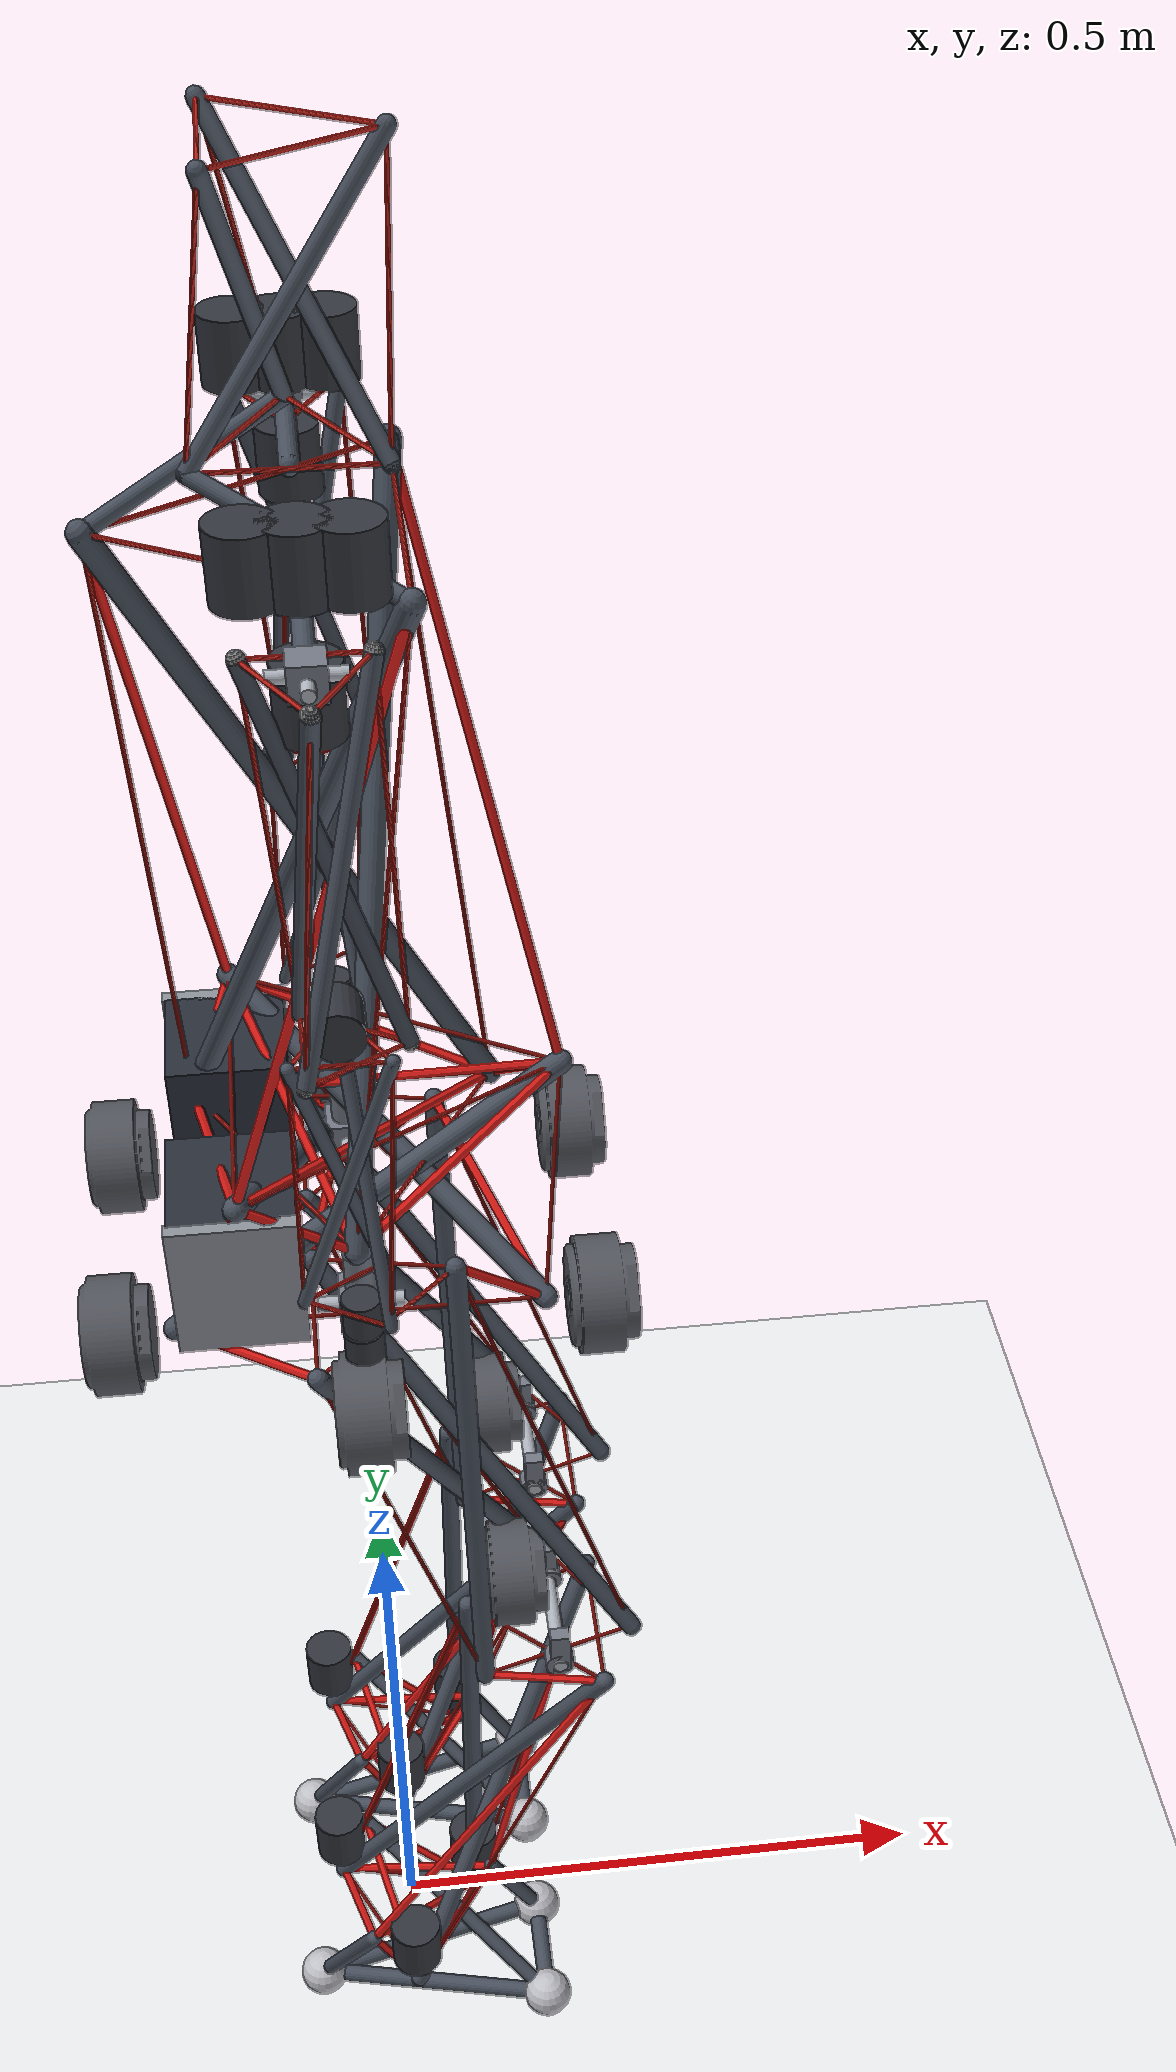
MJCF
<mujoco model="Hybrid Tensegrity Humanoid">
  <compiler angle="radian" autolimits="true" meshdir="assets"/>
  <option timestep="0.004" integrator="implicitfast" solver="Newton" iterations="60"/>
  <visual><global offwidth="1600" offheight="1200" realtime="0.3"/><map force="0.005"/></visual>
  <asset>
    <mesh name="ak70" file="ak70_10.stl"/>
    <mesh name="ak60" file="ak60_6.stl"/>
    <texture name="grid" type="2d" builtin="checker" rgb1="0.88 0.89 0.90" rgb2="0.96 0.96 0.97" width="512" height="512"/>
    <material name="grid" texture="grid" texrepeat="10 10"/>
  </asset>
  <default>
    <joint damping="1.5" armature="0.02" limited="true"/>
    <motor ctrllimited="true" ctrlrange="-1 1"/>
    <tendon rgba="0.82 0.10 0.08 1" width="0.0036"/>
  </default>
  <worldbody>
    <light pos="1.5 -1.5 3" dir="-0.35 0.35 -1" directional="true"/>
    <light pos="-2 1.5 2.5" dir="0.5 -0.4 -1" directional="true" diffuse="0.35 0.35 0.35"/>
    <geom name="floor" type="plane" size="8 8 0.1" material="grid" contype="1" conaffinity="1" friction="1.2 0.01 0.001"/>
    <body name="pelvis" pos="0 0 0.93900">
      <freejoint name="root"/>
      <geom type="capsule" size="0.009" mass="0" contype="0" conaffinity="0" rgba="0.28 0.31 0.36 1" fromto="0.00000 0.16000 -0.08000 -0.08048 -0.13828 0.08000"/>
      <geom type="capsule" size="0.009" mass="0" contype="0" conaffinity="0" rgba="0.28 0.31 0.36 1" fromto="-0.13856 -0.08000 -0.08000 0.16000 -0.00056 0.08000"/>
      <geom type="capsule" size="0.009" mass="0" contype="0" conaffinity="0" rgba="0.28 0.31 0.36 1" fromto="0.13856 -0.08000 -0.08000 -0.07952 0.13884 0.08000"/>
      <geom type="capsule" size="0.0016" mass="0" group="2" contype="0" conaffinity="0" rgba="0.72 0.13 0.10 1" fromto="0.00000 0.16000 -0.08000 -0.13856 -0.08000 -0.08000"/>
      <geom type="capsule" size="0.0016" mass="0" group="2" contype="0" conaffinity="0" rgba="0.72 0.13 0.10 1" fromto="-0.07952 0.13884 0.08000 -0.08048 -0.13828 0.08000"/>
      <geom type="capsule" size="0.0016" mass="0" group="2" contype="0" conaffinity="0" rgba="0.72 0.13 0.10 1" fromto="0.00000 0.16000 -0.08000 -0.07952 0.13884 0.08000"/>
      <geom type="capsule" size="0.0016" mass="0" group="2" contype="0" conaffinity="0" rgba="0.72 0.13 0.10 1" fromto="-0.13856 -0.08000 -0.08000 0.13856 -0.08000 -0.08000"/>
      <geom type="capsule" size="0.0016" mass="0" group="2" contype="0" conaffinity="0" rgba="0.72 0.13 0.10 1" fromto="-0.08048 -0.13828 0.08000 0.16000 -0.00056 0.08000"/>
      <geom type="capsule" size="0.0016" mass="0" group="2" contype="0" conaffinity="0" rgba="0.72 0.13 0.10 1" fromto="-0.13856 -0.08000 -0.08000 -0.08048 -0.13828 0.08000"/>
      <geom type="capsule" size="0.0016" mass="0" group="2" contype="0" conaffinity="0" rgba="0.72 0.13 0.10 1" fromto="0.13856 -0.08000 -0.08000 0.00000 0.16000 -0.08000"/>
      <geom type="capsule" size="0.0016" mass="0" group="2" contype="0" conaffinity="0" rgba="0.72 0.13 0.10 1" fromto="0.16000 -0.00056 0.08000 -0.07952 0.13884 0.08000"/>
      <geom type="capsule" size="0.0016" mass="0" group="2" contype="0" conaffinity="0" rgba="0.72 0.13 0.10 1" fromto="0.13856 -0.08000 -0.08000 0.16000 -0.00056 0.08000"/>
      <site name="pelv_b0" pos="0.00000 0.16000 -0.08000" size="0.006"/>
      <site name="pelv_t0" pos="-0.07952 0.13884 0.08000" size="0.006"/>
      <site name="pelv_b1" pos="-0.13856 -0.08000 -0.08000" size="0.006"/>
      <site name="pelv_t1" pos="-0.08048 -0.13828 0.08000" size="0.006"/>
      <site name="pelv_b2" pos="0.13856 -0.08000 -0.08000" size="0.006"/>
      <site name="pelv_t2" pos="0.16000 -0.00056 0.08000" size="0.006"/>
      <geom type="mesh" mesh="ak70" mass="0" contype="0" conaffinity="0" rgba="0.32 0.33 0.36 1" pos="0.17754 0.10250 -0.06000" xyaxes="0 0 1 0 1 0"/>
      <geom type="mesh" mesh="ak70" mass="0" contype="0" conaffinity="0" rgba="0.32 0.33 0.36 1" pos="0.00000 0.20500 -0.06000" xyaxes="0 0 1 0 1 0"/>
      <geom type="mesh" mesh="ak70" mass="0" contype="0" conaffinity="0" rgba="0.32 0.33 0.36 1" pos="-0.17754 0.10250 -0.06000" xyaxes="0 0 1 0 1 0"/>
      <geom type="mesh" mesh="ak70" mass="0" contype="0" conaffinity="0" rgba="0.32 0.33 0.36 1" pos="-0.17754 -0.10250 -0.06000" xyaxes="0 0 1 0 1 0"/>
      <geom type="mesh" mesh="ak70" mass="0" contype="0" conaffinity="0" rgba="0.32 0.33 0.36 1" pos="-0.00000 -0.20500 -0.06000" xyaxes="0 0 1 0 1 0"/>
      <geom type="mesh" mesh="ak70" mass="0" contype="0" conaffinity="0" rgba="0.32 0.33 0.36 1" pos="0.17754 -0.10250 -0.06000" xyaxes="0 0 1 0 1 0"/>
      <body name="battery_l" pos="-0.08500 0.08500 0.01000">
        <geom name="battery_l_pack" type="box" size="0.045 0.048 0.055" mass="2.5" contype="0" conaffinity="0" rgba="0.16 0.18 0.22 1"/>
        <geom type="box" size="0.047 0.006 0.055" mass="0.05" contype="0" conaffinity="0" rgba="0.55 0.57 0.60 1" pos="0 0.052 0"/>
      </body>
      <body name="battery_r" pos="-0.08500 -0.08500 0.01000">
        <geom name="battery_r_pack" type="box" size="0.045 0.048 0.055" mass="2.5" contype="0" conaffinity="0" rgba="0.16 0.18 0.22 1"/>
        <geom type="box" size="0.047 0.006 0.055" mass="0.05" contype="0" conaffinity="0" rgba="0.55 0.57 0.60 1" pos="0 -0.052 0"/>
      </body>
      <site name="hip_anchor_l" pos="0.00000 0.10000 -0.05000" size="0.007"/>
      <geom type="cylinder" size="0.011 0.022" mass="0" contype="0" conaffinity="0" rgba="0.45 0.47 0.52 1" pos="0.00000 0.10000 -0.02400"/>
      <geom type="cylinder" size="0.006 0.015" mass="0" contype="0" conaffinity="0" rgba="0.68 0.70 0.74 1" pos="0.00000 0.10000 -0.03800"/>
      <site name="hip_anchor_r" pos="0.00000 -0.10000 -0.05000" size="0.007"/>
      <geom type="cylinder" size="0.011 0.022" mass="0" contype="0" conaffinity="0" rgba="0.45 0.47 0.52 1" pos="0.00000 -0.10000 -0.02400"/>
      <geom type="cylinder" size="0.006 0.015" mass="0" contype="0" conaffinity="0" rgba="0.68 0.70 0.74 1" pos="0.00000 -0.10000 -0.03800"/>
      <inertial pos="-0.00653 0.00000 -0.03100" mass="4.5920" fullinertia="0.091199 0.091083 0.154922 -0.000000 0.003930 0.000000"/>
      <body name="thigh_l" pos="0.00000 0.10000 -0.05000">
        <joint name="hip_yaw_l" type="hinge" axis="0 0 1" range="-0.8 0.8"/>
        <joint name="hip_roll_l" type="hinge" axis="1 0 0" range="-0.6 0.6"/>
        <joint name="hip_pitch_l" type="hinge" axis="0 -1 0" range="-1.8 1.0"/>
        <geom type="capsule" size="0.008" mass="0" contype="0" conaffinity="0" rgba="0.28 0.31 0.36 1" fromto="0.13716 0.07500 -0.37575 -0.03544 -0.06482 -0.01294"/>
        <geom type="capsule" size="0.008" mass="0" contype="0" conaffinity="0" rgba="0.28 0.31 0.36 1" fromto="0.07615 -0.03750 -0.39802 0.07045 -0.00026 0.02572"/>
        <geom type="capsule" size="0.008" mass="0" contype="0" conaffinity="0" rgba="0.28 0.31 0.36 1" fromto="0.19817 -0.03750 -0.35348 -0.03501 0.06508 -0.01278"/>
        <geom type="capsule" size="0.0016" mass="0" group="2" contype="0" conaffinity="0" rgba="0.72 0.13 0.10 1" fromto="0.13716 0.07500 -0.37575 0.07615 -0.03750 -0.39802"/>
        <geom type="capsule" size="0.0016" mass="0" group="2" contype="0" conaffinity="0" rgba="0.72 0.13 0.10 1" fromto="-0.03501 0.06508 -0.01278 -0.03544 -0.06482 -0.01294"/>
        <geom type="capsule" size="0.0016" mass="0" group="2" contype="0" conaffinity="0" rgba="0.72 0.13 0.10 1" fromto="0.13716 0.07500 -0.37575 -0.03501 0.06508 -0.01278"/>
        <geom type="capsule" size="0.0016" mass="0" group="2" contype="0" conaffinity="0" rgba="0.72 0.13 0.10 1" fromto="0.07615 -0.03750 -0.39802 0.19817 -0.03750 -0.35348"/>
        <geom type="capsule" size="0.0016" mass="0" group="2" contype="0" conaffinity="0" rgba="0.72 0.13 0.10 1" fromto="-0.03544 -0.06482 -0.01294 0.07045 -0.00026 0.02572"/>
        <geom type="capsule" size="0.0016" mass="0" group="2" contype="0" conaffinity="0" rgba="0.72 0.13 0.10 1" fromto="0.07615 -0.03750 -0.39802 -0.03544 -0.06482 -0.01294"/>
        <geom type="capsule" size="0.0016" mass="0" group="2" contype="0" conaffinity="0" rgba="0.72 0.13 0.10 1" fromto="0.19817 -0.03750 -0.35348 0.13716 0.07500 -0.37575"/>
        <geom type="capsule" size="0.0016" mass="0" group="2" contype="0" conaffinity="0" rgba="0.72 0.13 0.10 1" fromto="0.07045 -0.00026 0.02572 -0.03501 0.06508 -0.01278"/>
        <geom type="capsule" size="0.0016" mass="0" group="2" contype="0" conaffinity="0" rgba="0.72 0.13 0.10 1" fromto="0.19817 -0.03750 -0.35348 0.07045 -0.00026 0.02572"/>
        <site name="th_l_b0" pos="0.13716 0.07500 -0.37575" size="0.006"/>
        <site name="th_l_t0" pos="-0.03501 0.06508 -0.01278" size="0.006"/>
        <site name="th_l_b1" pos="0.07615 -0.03750 -0.39802" size="0.006"/>
        <site name="th_l_t1" pos="-0.03544 -0.06482 -0.01294" size="0.006"/>
        <site name="th_l_b2" pos="0.19817 -0.03750 -0.35348" size="0.006"/>
        <site name="th_l_t2" pos="0.07045 -0.00026 0.02572" size="0.006"/>
        <geom type="box" size="0.016 0.016 0.016" mass="0" contype="0" conaffinity="0" rgba="0.45 0.47 0.52 1" pos="0 0 0"/>
        <geom type="cylinder" size="0.006 0.032" mass="0" contype="0" conaffinity="0" rgba="0.68 0.70 0.74 1" pos="0 0 0" xyaxes="0 0 1 0 1 0"/>
        <geom type="cylinder" size="0.006 0.032" mass="0" contype="0" conaffinity="0" rgba="0.68 0.70 0.74 1" pos="0 0 0" xyaxes="0 0 1 1 0 0"/>
        <geom type="box" size="0.008 0.006 0.020" mass="0" contype="0" conaffinity="0" rgba="0.45 0.47 0.52 1" pos="0.13716 0.04800 -0.36175"/>
        <geom type="box" size="0.008 0.006 0.020" mass="0" contype="0" conaffinity="0" rgba="0.45 0.47 0.52 1" pos="0.13716 -0.04800 -0.36175"/>
        <geom type="mesh" mesh="ak70" mass="0" contype="0" conaffinity="0" rgba="0.32 0.33 0.36 1" pos="0.10665 0.01875 -0.33689" xyaxes="0 0 1 0 1 0"/>
        <inertial pos="0.07832 0.00779 -0.23314" mass="1.2510" fullinertia="0.025316 0.026930 0.004641 -0.000276 0.005375 0.001011"/>
        <body name="shank_l" pos="0.13716 0.00000 -0.37575">
          <joint name="knee_l" type="hinge" axis="0 -1 0" range="-0.1 2.2"/>
          <geom type="capsule" size="0.008" mass="0" contype="0" conaffinity="0" rgba="0.28 0.31 0.36 1" fromto="-0.19865 0.03750 -0.38233 0.03529 -0.06508 -0.01200"/>
          <geom type="capsule" size="0.008" mass="0" contype="0" conaffinity="0" rgba="0.28 0.31 0.36 1" fromto="-0.13716 -0.07500 -0.40325 0.03572 0.06482 -0.01215"/>
          <geom type="capsule" size="0.008" mass="0" contype="0" conaffinity="0" rgba="0.28 0.31 0.36 1" fromto="-0.07567 0.03750 -0.42416 -0.07100 0.00026 0.02415"/>
          <geom type="capsule" size="0.0016" mass="0" group="2" contype="0" conaffinity="0" rgba="0.72 0.13 0.10 1" fromto="-0.19865 0.03750 -0.38233 -0.13716 -0.07500 -0.40325"/>
          <geom type="capsule" size="0.0016" mass="0" group="2" contype="0" conaffinity="0" rgba="0.72 0.13 0.10 1" fromto="-0.07100 0.00026 0.02415 0.03529 -0.06508 -0.01200"/>
          <geom type="capsule" size="0.0016" mass="0" group="2" contype="0" conaffinity="0" rgba="0.72 0.13 0.10 1" fromto="-0.19865 0.03750 -0.38233 -0.07100 0.00026 0.02415"/>
          <geom type="capsule" size="0.0016" mass="0" group="2" contype="0" conaffinity="0" rgba="0.72 0.13 0.10 1" fromto="-0.13716 -0.07500 -0.40325 -0.07567 0.03750 -0.42416"/>
          <geom type="capsule" size="0.0016" mass="0" group="2" contype="0" conaffinity="0" rgba="0.72 0.13 0.10 1" fromto="0.03529 -0.06508 -0.01200 0.03572 0.06482 -0.01215"/>
          <geom type="capsule" size="0.0016" mass="0" group="2" contype="0" conaffinity="0" rgba="0.72 0.13 0.10 1" fromto="-0.13716 -0.07500 -0.40325 0.03529 -0.06508 -0.01200"/>
          <geom type="capsule" size="0.0016" mass="0" group="2" contype="0" conaffinity="0" rgba="0.72 0.13 0.10 1" fromto="-0.07567 0.03750 -0.42416 -0.19865 0.03750 -0.38233"/>
          <geom type="capsule" size="0.0016" mass="0" group="2" contype="0" conaffinity="0" rgba="0.72 0.13 0.10 1" fromto="0.03572 0.06482 -0.01215 -0.07100 0.00026 0.02415"/>
          <geom type="capsule" size="0.0016" mass="0" group="2" contype="0" conaffinity="0" rgba="0.72 0.13 0.10 1" fromto="-0.07567 0.03750 -0.42416 0.03572 0.06482 -0.01215"/>
          <site name="sh_l_b0" pos="-0.19865 0.03750 -0.38233" size="0.006"/>
          <site name="sh_l_t0" pos="-0.07100 0.00026 0.02415" size="0.006"/>
          <site name="sh_l_b1" pos="-0.13716 -0.07500 -0.40325" size="0.006"/>
          <site name="sh_l_t1" pos="0.03529 -0.06508 -0.01200" size="0.006"/>
          <site name="sh_l_b2" pos="-0.07567 0.03750 -0.42416" size="0.006"/>
          <site name="sh_l_t2" pos="0.03572 0.06482 -0.01215" size="0.006"/>
          <geom type="cylinder" size="0.006 0.055" mass="0" contype="0" conaffinity="0" rgba="0.68 0.70 0.74 1" pos="0 0 0" xyaxes="0 0 1 1 0 0"/>
          <geom type="cylinder" size="0.012 0.008" mass="0" contype="0" conaffinity="0" rgba="0.45 0.47 0.52 1" pos="0 0.04600 0" xyaxes="0 0 1 1 0 0"/>
          <geom type="cylinder" size="0.012 0.008" mass="0" contype="0" conaffinity="0" rgba="0.45 0.47 0.52 1" pos="0 -0.04600 0" xyaxes="0 0 1 1 0 0"/>
          <geom type="cylinder" size="0.022 0.024" mass="0" contype="0" conaffinity="0" rgba="0.20 0.21 0.24 1" pos="-0.19865 0.03750 -0.32233"/>
          <geom type="cylinder" size="0.022 0.024" mass="0" contype="0" conaffinity="0" rgba="0.20 0.21 0.24 1" pos="-0.13716 -0.07500 -0.34325"/>
          <geom type="cylinder" size="0.022 0.024" mass="0" contype="0" conaffinity="0" rgba="0.20 0.21 0.24 1" pos="-0.07567 0.03750 -0.36416"/>
          <inertial pos="-0.09488 -0.00000 -0.24498" mass="1.0770" fullinertia="0.020941 0.022766 0.007421 0.000000 -0.004289 -0.000000"/>
        </body>
      </body>
      <body name="thigh_r" pos="0.00000 -0.10000 -0.05000">
        <joint name="hip_yaw_r" type="hinge" axis="0 0 1" range="-0.8 0.8"/>
        <joint name="hip_roll_r" type="hinge" axis="1 0 0" range="-0.6 0.6"/>
        <joint name="hip_pitch_r" type="hinge" axis="0 -1 0" range="-1.8 1.0"/>
        <geom type="capsule" size="0.008" mass="0" contype="0" conaffinity="0" rgba="0.28 0.31 0.36 1" fromto="0.13716 0.07500 -0.37575 -0.03544 -0.06482 -0.01294"/>
        <geom type="capsule" size="0.008" mass="0" contype="0" conaffinity="0" rgba="0.28 0.31 0.36 1" fromto="0.07615 -0.03750 -0.39802 0.07045 -0.00026 0.02572"/>
        <geom type="capsule" size="0.008" mass="0" contype="0" conaffinity="0" rgba="0.28 0.31 0.36 1" fromto="0.19817 -0.03750 -0.35348 -0.03501 0.06508 -0.01278"/>
        <geom type="capsule" size="0.0016" mass="0" group="2" contype="0" conaffinity="0" rgba="0.72 0.13 0.10 1" fromto="0.13716 0.07500 -0.37575 0.07615 -0.03750 -0.39802"/>
        <geom type="capsule" size="0.0016" mass="0" group="2" contype="0" conaffinity="0" rgba="0.72 0.13 0.10 1" fromto="-0.03501 0.06508 -0.01278 -0.03544 -0.06482 -0.01294"/>
        <geom type="capsule" size="0.0016" mass="0" group="2" contype="0" conaffinity="0" rgba="0.72 0.13 0.10 1" fromto="0.13716 0.07500 -0.37575 -0.03501 0.06508 -0.01278"/>
        <geom type="capsule" size="0.0016" mass="0" group="2" contype="0" conaffinity="0" rgba="0.72 0.13 0.10 1" fromto="0.07615 -0.03750 -0.39802 0.19817 -0.03750 -0.35348"/>
        <geom type="capsule" size="0.0016" mass="0" group="2" contype="0" conaffinity="0" rgba="0.72 0.13 0.10 1" fromto="-0.03544 -0.06482 -0.01294 0.07045 -0.00026 0.02572"/>
        <geom type="capsule" size="0.0016" mass="0" group="2" contype="0" conaffinity="0" rgba="0.72 0.13 0.10 1" fromto="0.07615 -0.03750 -0.39802 -0.03544 -0.06482 -0.01294"/>
        <geom type="capsule" size="0.0016" mass="0" group="2" contype="0" conaffinity="0" rgba="0.72 0.13 0.10 1" fromto="0.19817 -0.03750 -0.35348 0.13716 0.07500 -0.37575"/>
        <geom type="capsule" size="0.0016" mass="0" group="2" contype="0" conaffinity="0" rgba="0.72 0.13 0.10 1" fromto="0.07045 -0.00026 0.02572 -0.03501 0.06508 -0.01278"/>
        <geom type="capsule" size="0.0016" mass="0" group="2" contype="0" conaffinity="0" rgba="0.72 0.13 0.10 1" fromto="0.19817 -0.03750 -0.35348 0.07045 -0.00026 0.02572"/>
        <site name="th_r_b0" pos="0.13716 0.07500 -0.37575" size="0.006"/>
        <site name="th_r_t0" pos="-0.03501 0.06508 -0.01278" size="0.006"/>
        <site name="th_r_b1" pos="0.07615 -0.03750 -0.39802" size="0.006"/>
        <site name="th_r_t1" pos="-0.03544 -0.06482 -0.01294" size="0.006"/>
        <site name="th_r_b2" pos="0.19817 -0.03750 -0.35348" size="0.006"/>
        <site name="th_r_t2" pos="0.07045 -0.00026 0.02572" size="0.006"/>
        <geom type="box" size="0.016 0.016 0.016" mass="0" contype="0" conaffinity="0" rgba="0.45 0.47 0.52 1" pos="0 0 0"/>
        <geom type="cylinder" size="0.006 0.032" mass="0" contype="0" conaffinity="0" rgba="0.68 0.70 0.74 1" pos="0 0 0" xyaxes="0 0 1 0 1 0"/>
        <geom type="cylinder" size="0.006 0.032" mass="0" contype="0" conaffinity="0" rgba="0.68 0.70 0.74 1" pos="0 0 0" xyaxes="0 0 1 1 0 0"/>
        <geom type="box" size="0.008 0.006 0.020" mass="0" contype="0" conaffinity="0" rgba="0.45 0.47 0.52 1" pos="0.13716 0.04800 -0.36175"/>
        <geom type="box" size="0.008 0.006 0.020" mass="0" contype="0" conaffinity="0" rgba="0.45 0.47 0.52 1" pos="0.13716 -0.04800 -0.36175"/>
        <geom type="mesh" mesh="ak70" mass="0" contype="0" conaffinity="0" rgba="0.32 0.33 0.36 1" pos="0.10665 0.01875 -0.33689" xyaxes="0 0 1 0 1 0"/>
        <inertial pos="0.07832 0.00779 -0.23314" mass="1.2510" fullinertia="0.025316 0.026930 0.004641 -0.000276 0.005375 0.001011"/>
        <body name="shank_r" pos="0.13716 0.00000 -0.37575">
          <joint name="knee_r" type="hinge" axis="0 -1 0" range="-0.1 2.2"/>
          <geom type="capsule" size="0.008" mass="0" contype="0" conaffinity="0" rgba="0.28 0.31 0.36 1" fromto="-0.19865 0.03750 -0.38233 0.03529 -0.06508 -0.01200"/>
          <geom type="capsule" size="0.008" mass="0" contype="0" conaffinity="0" rgba="0.28 0.31 0.36 1" fromto="-0.13716 -0.07500 -0.40325 0.03572 0.06482 -0.01215"/>
          <geom type="capsule" size="0.008" mass="0" contype="0" conaffinity="0" rgba="0.28 0.31 0.36 1" fromto="-0.07567 0.03750 -0.42416 -0.07100 0.00026 0.02415"/>
          <geom type="capsule" size="0.0016" mass="0" group="2" contype="0" conaffinity="0" rgba="0.72 0.13 0.10 1" fromto="-0.19865 0.03750 -0.38233 -0.13716 -0.07500 -0.40325"/>
          <geom type="capsule" size="0.0016" mass="0" group="2" contype="0" conaffinity="0" rgba="0.72 0.13 0.10 1" fromto="-0.07100 0.00026 0.02415 0.03529 -0.06508 -0.01200"/>
          <geom type="capsule" size="0.0016" mass="0" group="2" contype="0" conaffinity="0" rgba="0.72 0.13 0.10 1" fromto="-0.19865 0.03750 -0.38233 -0.07100 0.00026 0.02415"/>
          <geom type="capsule" size="0.0016" mass="0" group="2" contype="0" conaffinity="0" rgba="0.72 0.13 0.10 1" fromto="-0.13716 -0.07500 -0.40325 -0.07567 0.03750 -0.42416"/>
          <geom type="capsule" size="0.0016" mass="0" group="2" contype="0" conaffinity="0" rgba="0.72 0.13 0.10 1" fromto="0.03529 -0.06508 -0.01200 0.03572 0.06482 -0.01215"/>
          <geom type="capsule" size="0.0016" mass="0" group="2" contype="0" conaffinity="0" rgba="0.72 0.13 0.10 1" fromto="-0.13716 -0.07500 -0.40325 0.03529 -0.06508 -0.01200"/>
          <geom type="capsule" size="0.0016" mass="0" group="2" contype="0" conaffinity="0" rgba="0.72 0.13 0.10 1" fromto="-0.07567 0.03750 -0.42416 -0.19865 0.03750 -0.38233"/>
          <geom type="capsule" size="0.0016" mass="0" group="2" contype="0" conaffinity="0" rgba="0.72 0.13 0.10 1" fromto="0.03572 0.06482 -0.01215 -0.07100 0.00026 0.02415"/>
          <geom type="capsule" size="0.0016" mass="0" group="2" contype="0" conaffinity="0" rgba="0.72 0.13 0.10 1" fromto="-0.07567 0.03750 -0.42416 0.03572 0.06482 -0.01215"/>
          <site name="sh_r_b0" pos="-0.19865 0.03750 -0.38233" size="0.006"/>
          <site name="sh_r_t0" pos="-0.07100 0.00026 0.02415" size="0.006"/>
          <site name="sh_r_b1" pos="-0.13716 -0.07500 -0.40325" size="0.006"/>
          <site name="sh_r_t1" pos="0.03529 -0.06508 -0.01200" size="0.006"/>
          <site name="sh_r_b2" pos="-0.07567 0.03750 -0.42416" size="0.006"/>
          <site name="sh_r_t2" pos="0.03572 0.06482 -0.01215" size="0.006"/>
          <geom type="cylinder" size="0.006 0.055" mass="0" contype="0" conaffinity="0" rgba="0.68 0.70 0.74 1" pos="0 0 0" xyaxes="0 0 1 1 0 0"/>
          <geom type="cylinder" size="0.012 0.008" mass="0" contype="0" conaffinity="0" rgba="0.45 0.47 0.52 1" pos="0 0.04600 0" xyaxes="0 0 1 1 0 0"/>
          <geom type="cylinder" size="0.012 0.008" mass="0" contype="0" conaffinity="0" rgba="0.45 0.47 0.52 1" pos="0 -0.04600 0" xyaxes="0 0 1 1 0 0"/>
          <geom type="cylinder" size="0.022 0.024" mass="0" contype="0" conaffinity="0" rgba="0.20 0.21 0.24 1" pos="-0.19865 0.03750 -0.32233"/>
          <geom type="cylinder" size="0.022 0.024" mass="0" contype="0" conaffinity="0" rgba="0.20 0.21 0.24 1" pos="-0.13716 -0.07500 -0.34325"/>
          <geom type="cylinder" size="0.022 0.024" mass="0" contype="0" conaffinity="0" rgba="0.20 0.21 0.24 1" pos="-0.07567 0.03750 -0.36416"/>
          <inertial pos="-0.09488 -0.00000 -0.24498" mass="1.0770" fullinertia="0.020941 0.022766 0.007421 0.000000 -0.004289 -0.000000"/>
        </body>
      </body>
    </body>
    <body name="foot_l" pos="0.00000 0.10000 0.04400">
      <freejoint/>
      <geom name="pad_l0" type="sphere" size="0.022" mass="0" contype="1" conaffinity="1" friction="1.2 0.01 0.001" rgba="0.75 0.75 0.78 1" pos="-0.09000 0.00000 -0.02200"/>
      <geom name="pad_l1" type="sphere" size="0.022" mass="0" contype="1" conaffinity="1" friction="1.2 0.01 0.001" rgba="0.75 0.75 0.78 1" pos="0.12000 0.05000 -0.02200"/>
      <geom name="pad_l2" type="sphere" size="0.022" mass="0" contype="1" conaffinity="1" friction="1.2 0.01 0.001" rgba="0.75 0.75 0.78 1" pos="0.12000 -0.05000 -0.02200"/>
      <geom type="capsule" size="0.008" mass="0" contype="0" conaffinity="0" rgba="0.28 0.31 0.36 1" fromto="-0.09000 0.00000 -0.02200 0.12000 0.05000 -0.02200"/>
      <geom type="capsule" size="0.008" mass="0" contype="0" conaffinity="0" rgba="0.28 0.31 0.36 1" fromto="0.12000 0.05000 -0.02200 0.12000 -0.05000 -0.02200"/>
      <geom type="capsule" size="0.008" mass="0" contype="0" conaffinity="0" rgba="0.28 0.31 0.36 1" fromto="0.12000 -0.05000 -0.02200 -0.09000 0.00000 -0.02200"/>
      <geom type="capsule" size="0.007" mass="0" contype="0" conaffinity="0" rgba="0.28 0.31 0.36 1" fromto="-0.09000 0.00000 -0.02200 -0.03750 -0.06495 0.12100"/>
      <geom type="capsule" size="0.007" mass="0" contype="0" conaffinity="0" rgba="0.28 0.31 0.36 1" fromto="0.12000 0.05000 -0.02200 0.07500 -0.00000 0.12100"/>
      <geom type="capsule" size="0.007" mass="0" contype="0" conaffinity="0" rgba="0.28 0.31 0.36 1" fromto="0.12000 -0.05000 -0.02200 -0.03750 0.06495 0.12100"/>
      <site name="mast_l0" pos="-0.03750 0.06495 0.12100" size="0.006"/>
      <site name="plate_l0" pos="-0.09000 0.00000 -0.02200" size="0.005"/>
      <site name="mast_l1" pos="-0.03750 -0.06495 0.12100" size="0.006"/>
      <site name="plate_l1" pos="0.12000 0.05000 -0.02200" size="0.005"/>
      <site name="mast_l2" pos="0.07500 -0.00000 0.12100" size="0.006"/>
      <site name="plate_l2" pos="0.12000 -0.05000 -0.02200" size="0.005"/>
      <inertial pos="0.02000 0.00000 0.03000" mass="0.4500" fullinertia="0.002843 0.002843 0.003645 0.000000 0.000000 0.000000"/>
    </body>
    <body name="foot_r" pos="0.00000 -0.10000 0.04400">
      <freejoint/>
      <geom name="pad_r0" type="sphere" size="0.022" mass="0" contype="1" conaffinity="1" friction="1.2 0.01 0.001" rgba="0.75 0.75 0.78 1" pos="-0.09000 0.00000 -0.02200"/>
      <geom name="pad_r1" type="sphere" size="0.022" mass="0" contype="1" conaffinity="1" friction="1.2 0.01 0.001" rgba="0.75 0.75 0.78 1" pos="0.12000 0.05000 -0.02200"/>
      <geom name="pad_r2" type="sphere" size="0.022" mass="0" contype="1" conaffinity="1" friction="1.2 0.01 0.001" rgba="0.75 0.75 0.78 1" pos="0.12000 -0.05000 -0.02200"/>
      <geom type="capsule" size="0.008" mass="0" contype="0" conaffinity="0" rgba="0.28 0.31 0.36 1" fromto="-0.09000 0.00000 -0.02200 0.12000 0.05000 -0.02200"/>
      <geom type="capsule" size="0.008" mass="0" contype="0" conaffinity="0" rgba="0.28 0.31 0.36 1" fromto="0.12000 0.05000 -0.02200 0.12000 -0.05000 -0.02200"/>
      <geom type="capsule" size="0.008" mass="0" contype="0" conaffinity="0" rgba="0.28 0.31 0.36 1" fromto="0.12000 -0.05000 -0.02200 -0.09000 0.00000 -0.02200"/>
      <geom type="capsule" size="0.007" mass="0" contype="0" conaffinity="0" rgba="0.28 0.31 0.36 1" fromto="-0.09000 0.00000 -0.02200 -0.03750 -0.06495 0.12100"/>
      <geom type="capsule" size="0.007" mass="0" contype="0" conaffinity="0" rgba="0.28 0.31 0.36 1" fromto="0.12000 0.05000 -0.02200 0.07500 -0.00000 0.12100"/>
      <geom type="capsule" size="0.007" mass="0" contype="0" conaffinity="0" rgba="0.28 0.31 0.36 1" fromto="0.12000 -0.05000 -0.02200 -0.03750 0.06495 0.12100"/>
      <site name="mast_r0" pos="-0.03750 0.06495 0.12100" size="0.006"/>
      <site name="plate_r0" pos="-0.09000 0.00000 -0.02200" size="0.005"/>
      <site name="mast_r1" pos="-0.03750 -0.06495 0.12100" size="0.006"/>
      <site name="plate_r1" pos="0.12000 0.05000 -0.02200" size="0.005"/>
      <site name="mast_r2" pos="0.07500 -0.00000 0.12100" size="0.006"/>
      <site name="plate_r2" pos="0.12000 -0.05000 -0.02200" size="0.005"/>
      <inertial pos="0.02000 0.00000 0.03000" mass="0.4500" fullinertia="0.002843 0.002843 0.003645 0.000000 0.000000 0.000000"/>
    </body>
    <body name="torso" pos="0 0 1.23900">
      <freejoint/>
      <geom type="capsule" size="0.009" mass="0" contype="0" conaffinity="0" rgba="0.28 0.31 0.36 1" fromto="-0.11258 0.06500 -0.27500 0.06461 -0.11281 0.21000"/>
      <geom type="capsule" size="0.009" mass="0" contype="0" conaffinity="0" rgba="0.28 0.31 0.36 1" fromto="-0.00000 -0.13000 -0.27500 0.06539 0.11236 0.21000"/>
      <geom type="capsule" size="0.009" mass="0" contype="0" conaffinity="0" rgba="0.28 0.31 0.36 1" fromto="0.11258 0.06500 -0.27500 -0.13000 0.00045 0.21000"/>
      <geom type="capsule" size="0.0016" mass="0" group="2" contype="0" conaffinity="0" rgba="0.72 0.13 0.10 1" fromto="-0.11258 0.06500 -0.27500 -0.00000 -0.13000 -0.27500"/>
      <geom type="capsule" size="0.0016" mass="0" group="2" contype="0" conaffinity="0" rgba="0.72 0.13 0.10 1" fromto="-0.13000 0.00045 0.21000 0.06461 -0.11281 0.21000"/>
      <geom type="capsule" size="0.0016" mass="0" group="2" contype="0" conaffinity="0" rgba="0.72 0.13 0.10 1" fromto="-0.11258 0.06500 -0.27500 -0.13000 0.00045 0.21000"/>
      <geom type="capsule" size="0.0016" mass="0" group="2" contype="0" conaffinity="0" rgba="0.72 0.13 0.10 1" fromto="-0.00000 -0.13000 -0.27500 0.11258 0.06500 -0.27500"/>
      <geom type="capsule" size="0.0016" mass="0" group="2" contype="0" conaffinity="0" rgba="0.72 0.13 0.10 1" fromto="0.06461 -0.11281 0.21000 0.06539 0.11236 0.21000"/>
      <geom type="capsule" size="0.0016" mass="0" group="2" contype="0" conaffinity="0" rgba="0.72 0.13 0.10 1" fromto="-0.00000 -0.13000 -0.27500 0.06461 -0.11281 0.21000"/>
      <geom type="capsule" size="0.0016" mass="0" group="2" contype="0" conaffinity="0" rgba="0.72 0.13 0.10 1" fromto="0.11258 0.06500 -0.27500 -0.11258 0.06500 -0.27500"/>
      <geom type="capsule" size="0.0016" mass="0" group="2" contype="0" conaffinity="0" rgba="0.72 0.13 0.10 1" fromto="0.06539 0.11236 0.21000 -0.13000 0.00045 0.21000"/>
      <geom type="capsule" size="0.0016" mass="0" group="2" contype="0" conaffinity="0" rgba="0.72 0.13 0.10 1" fromto="0.11258 0.06500 -0.27500 0.06539 0.11236 0.21000"/>
      <site name="torso_b0" pos="-0.11258 0.06500 -0.27500" size="0.006"/>
      <site name="torso_t0" pos="-0.13000 0.00045 0.21000" size="0.006"/>
      <site name="torso_b1" pos="-0.00000 -0.13000 -0.27500" size="0.006"/>
      <site name="torso_t1" pos="0.06461 -0.11281 0.21000" size="0.006"/>
      <site name="torso_b2" pos="0.11258 0.06500 -0.27500" size="0.006"/>
      <site name="torso_t2" pos="0.06539 0.11236 0.21000" size="0.006"/>
      <geom type="cylinder" size="0.022 0.024" mass="0" contype="0" conaffinity="0" rgba="0.20 0.21 0.24 1" pos="0.00000 0.16000 0.18000"/>
      <geom type="cylinder" size="0.022 0.024" mass="0" contype="0" conaffinity="0" rgba="0.20 0.21 0.24 1" pos="0.00000 -0.16000 0.18000"/>
      <geom type="capsule" size="0.006" mass="0" contype="0" conaffinity="0" rgba="0.28 0.31 0.36 1" fromto="-0.13000 0.00045 0.21000 0.00000 0.07000 0.26000"/>
      <geom type="capsule" size="0.006" mass="0" contype="0" conaffinity="0" rgba="0.28 0.31 0.36 1" fromto="0.06461 -0.11281 0.21000 -0.06062 -0.03500 0.26000"/>
      <geom type="capsule" size="0.006" mass="0" contype="0" conaffinity="0" rgba="0.28 0.31 0.36 1" fromto="0.06539 0.11236 0.21000 0.06062 -0.03500 0.26000"/>
      <body name="head" pos="0 0 0.35000">
        <geom type="capsule" size="0.006" mass="0" contype="0" conaffinity="0" rgba="0.28 0.31 0.36 1" fromto="0.00000 0.07000 -0.09000 -0.03521 -0.06050 0.09000"/>
        <geom type="capsule" size="0.006" mass="0" contype="0" conaffinity="0" rgba="0.28 0.31 0.36 1" fromto="-0.06062 -0.03500 -0.09000 0.07000 -0.00024 0.09000"/>
        <geom type="capsule" size="0.006" mass="0" contype="0" conaffinity="0" rgba="0.28 0.31 0.36 1" fromto="0.06062 -0.03500 -0.09000 -0.03479 0.06074 0.09000"/>
        <geom type="capsule" size="0.0016" mass="0" group="2" contype="0" conaffinity="0" rgba="0.72 0.13 0.10 1" fromto="0.00000 0.07000 -0.09000 -0.06062 -0.03500 -0.09000"/>
        <geom type="capsule" size="0.0016" mass="0" group="2" contype="0" conaffinity="0" rgba="0.72 0.13 0.10 1" fromto="-0.03479 0.06074 0.09000 -0.03521 -0.06050 0.09000"/>
        <geom type="capsule" size="0.0016" mass="0" group="2" contype="0" conaffinity="0" rgba="0.72 0.13 0.10 1" fromto="0.00000 0.07000 -0.09000 -0.03479 0.06074 0.09000"/>
        <geom type="capsule" size="0.0016" mass="0" group="2" contype="0" conaffinity="0" rgba="0.72 0.13 0.10 1" fromto="-0.06062 -0.03500 -0.09000 0.06062 -0.03500 -0.09000"/>
        <geom type="capsule" size="0.0016" mass="0" group="2" contype="0" conaffinity="0" rgba="0.72 0.13 0.10 1" fromto="-0.03521 -0.06050 0.09000 0.07000 -0.00024 0.09000"/>
        <geom type="capsule" size="0.0016" mass="0" group="2" contype="0" conaffinity="0" rgba="0.72 0.13 0.10 1" fromto="-0.06062 -0.03500 -0.09000 -0.03521 -0.06050 0.09000"/>
        <geom type="capsule" size="0.0016" mass="0" group="2" contype="0" conaffinity="0" rgba="0.72 0.13 0.10 1" fromto="0.06062 -0.03500 -0.09000 0.00000 0.07000 -0.09000"/>
        <geom type="capsule" size="0.0016" mass="0" group="2" contype="0" conaffinity="0" rgba="0.72 0.13 0.10 1" fromto="0.07000 -0.00024 0.09000 -0.03479 0.06074 0.09000"/>
        <geom type="capsule" size="0.0016" mass="0" group="2" contype="0" conaffinity="0" rgba="0.72 0.13 0.10 1" fromto="0.06062 -0.03500 -0.09000 0.07000 -0.00024 0.09000"/>
        <inertial pos="0.00000 0.00000 0.00000" mass="0.5000" fullinertia="0.002575 0.002575 0.002450 0.000000 0.000000 0.000000"/>
      </body>
      <geom type="cylinder" size="0.022 0.024" mass="0" contype="0" conaffinity="0" rgba="0.20 0.21 0.24 1" pos="-0.03000 0.15000 0.26000"/>
      <geom type="cylinder" size="0.022 0.024" mass="0" contype="0" conaffinity="0" rgba="0.20 0.21 0.24 1" pos="0.00000 0.15000 0.26000"/>
      <geom type="cylinder" size="0.022 0.024" mass="0" contype="0" conaffinity="0" rgba="0.20 0.21 0.24 1" pos="0.03000 0.15000 0.26000"/>
      <geom type="capsule" size="0.007" mass="0" contype="0" conaffinity="0" rgba="0.28 0.31 0.36 1" fromto="0 0.08000 0.21000 0 0.19000 0.21000"/>
      <geom type="capsule" size="0.005" mass="0" contype="0" conaffinity="0" rgba="0.28 0.31 0.36 1" fromto="0 0.10000 0.10000 0 0.18500 0.20000"/>
      <body name="upper_arm_l" pos="0.00000 0.19000 0.21000">
        <joint name="shoulder_yaw_l" type="hinge" axis="0 0 1" range="-1.5 1.5" stiffness="60.0" damping="2.5"/>
        <joint name="shoulder_roll_l" type="hinge" axis="1 0 0" range="-1.4 1.4" stiffness="60.0" damping="2.5"/>
        <joint name="shoulder_pitch_l" type="hinge" axis="0 -1 0" range="-2.5 1.5"/>
        <geom type="box" size="0.012 0.012 0.012" mass="0" contype="0" conaffinity="0" rgba="0.45 0.47 0.52 1" pos="0 0 0"/>
        <geom type="cylinder" size="0.0045 0.024" mass="0" contype="0" conaffinity="0" rgba="0.68 0.70 0.74 1" pos="0 0 0" xyaxes="0 0 1 0 1 0"/>
        <geom type="cylinder" size="0.0045 0.024" mass="0" contype="0" conaffinity="0" rgba="0.68 0.70 0.74 1" pos="0 0 0" xyaxes="0 0 1 1 0 0"/>
        <geom type="capsule" size="0.006" mass="0" contype="0" conaffinity="0" rgba="0.28 0.31 0.36 1" fromto="0.00000 -0.04500 0.00000 -0.02264 0.03889 -0.26000"/>
        <geom type="capsule" size="0.006" mass="0" contype="0" conaffinity="0" rgba="0.28 0.31 0.36 1" fromto="-0.03897 0.02250 0.00000 0.04500 0.00016 -0.26000"/>
        <geom type="capsule" size="0.006" mass="0" contype="0" conaffinity="0" rgba="0.28 0.31 0.36 1" fromto="0.03897 0.02250 0.00000 -0.02236 -0.03905 -0.26000"/>
        <geom type="capsule" size="0.0016" mass="0" group="2" contype="0" conaffinity="0" rgba="0.72 0.13 0.10 1" fromto="0.00000 -0.04500 0.00000 -0.03897 0.02250 0.00000"/>
        <geom type="capsule" size="0.0016" mass="0" group="2" contype="0" conaffinity="0" rgba="0.72 0.13 0.10 1" fromto="-0.02236 -0.03905 -0.26000 -0.02264 0.03889 -0.26000"/>
        <geom type="capsule" size="0.0016" mass="0" group="2" contype="0" conaffinity="0" rgba="0.72 0.13 0.10 1" fromto="0.00000 -0.04500 0.00000 -0.02236 -0.03905 -0.26000"/>
        <geom type="capsule" size="0.0016" mass="0" group="2" contype="0" conaffinity="0" rgba="0.72 0.13 0.10 1" fromto="-0.03897 0.02250 0.00000 0.03897 0.02250 0.00000"/>
        <geom type="capsule" size="0.0016" mass="0" group="2" contype="0" conaffinity="0" rgba="0.72 0.13 0.10 1" fromto="-0.02264 0.03889 -0.26000 0.04500 0.00016 -0.26000"/>
        <geom type="capsule" size="0.0016" mass="0" group="2" contype="0" conaffinity="0" rgba="0.72 0.13 0.10 1" fromto="-0.03897 0.02250 0.00000 -0.02264 0.03889 -0.26000"/>
        <geom type="capsule" size="0.0016" mass="0" group="2" contype="0" conaffinity="0" rgba="0.72 0.13 0.10 1" fromto="0.03897 0.02250 0.00000 0.00000 -0.04500 0.00000"/>
        <geom type="capsule" size="0.0016" mass="0" group="2" contype="0" conaffinity="0" rgba="0.72 0.13 0.10 1" fromto="0.04500 0.00016 -0.26000 -0.02236 -0.03905 -0.26000"/>
        <geom type="capsule" size="0.0016" mass="0" group="2" contype="0" conaffinity="0" rgba="0.72 0.13 0.10 1" fromto="0.03897 0.02250 0.00000 0.04500 0.00016 -0.26000"/>
        <site name="ua_l_b0" pos="0.00000 -0.04500 0.00000" size="0.006"/>
        <site name="ua_l_t0" pos="-0.02236 -0.03905 -0.26000" size="0.006"/>
        <site name="ua_l_b1" pos="-0.03897 0.02250 0.00000" size="0.006"/>
        <site name="ua_l_t1" pos="-0.02264 0.03889 -0.26000" size="0.006"/>
        <site name="ua_l_b2" pos="0.03897 0.02250 0.00000" size="0.006"/>
        <site name="ua_l_t2" pos="0.04500 0.00016 -0.26000" size="0.006"/>
        <inertial pos="0.00000 0.00000 -0.10484" mass="0.3100" fullinertia="0.002479 0.002479 0.000506 0.000000 0.000000 0.000000"/>
        <body name="forearm_l" pos="0 0 -0.26000">
          <joint name="elbow_l" type="hinge" axis="0 -1 0" range="-2.4 0.05"/>
          <geom type="cylinder" size="0.018 0.018" mass="0" contype="0" conaffinity="0" rgba="0.20 0.21 0.24 1" pos="0 0 0.02" xyaxes="0 0 1 1 0 0"/>
          <geom type="capsule" size="0.005" mass="0" contype="0" conaffinity="0" rgba="0.28 0.31 0.36 1" fromto="-0.03291 -0.01900 0.00000 0.01889 0.03298 -0.21320"/>
          <geom type="capsule" size="0.005" mass="0" contype="0" conaffinity="0" rgba="0.28 0.31 0.36 1" fromto="-0.00000 0.03800 0.00000 0.01911 -0.03284 -0.21320"/>
          <geom type="capsule" size="0.005" mass="0" contype="0" conaffinity="0" rgba="0.28 0.31 0.36 1" fromto="0.03291 -0.01900 0.00000 -0.03800 -0.00013 -0.21320"/>
          <geom type="capsule" size="0.0016" mass="0" group="2" contype="0" conaffinity="0" rgba="0.72 0.13 0.10 1" fromto="-0.03291 -0.01900 0.00000 -0.00000 0.03800 0.00000"/>
          <geom type="capsule" size="0.0016" mass="0" group="2" contype="0" conaffinity="0" rgba="0.72 0.13 0.10 1" fromto="-0.03800 -0.00013 -0.21320 0.01889 0.03298 -0.21320"/>
          <geom type="capsule" size="0.0016" mass="0" group="2" contype="0" conaffinity="0" rgba="0.72 0.13 0.10 1" fromto="-0.03291 -0.01900 0.00000 -0.03800 -0.00013 -0.21320"/>
          <geom type="capsule" size="0.0016" mass="0" group="2" contype="0" conaffinity="0" rgba="0.72 0.13 0.10 1" fromto="-0.00000 0.03800 0.00000 0.03291 -0.01900 0.00000"/>
          <geom type="capsule" size="0.0016" mass="0" group="2" contype="0" conaffinity="0" rgba="0.72 0.13 0.10 1" fromto="0.01889 0.03298 -0.21320 0.01911 -0.03284 -0.21320"/>
          <geom type="capsule" size="0.0016" mass="0" group="2" contype="0" conaffinity="0" rgba="0.72 0.13 0.10 1" fromto="-0.00000 0.03800 0.00000 0.01889 0.03298 -0.21320"/>
          <geom type="capsule" size="0.0016" mass="0" group="2" contype="0" conaffinity="0" rgba="0.72 0.13 0.10 1" fromto="0.03291 -0.01900 0.00000 -0.03291 -0.01900 0.00000"/>
          <geom type="capsule" size="0.0016" mass="0" group="2" contype="0" conaffinity="0" rgba="0.72 0.13 0.10 1" fromto="0.01911 -0.03284 -0.21320 -0.03800 -0.00013 -0.21320"/>
          <geom type="capsule" size="0.0016" mass="0" group="2" contype="0" conaffinity="0" rgba="0.72 0.13 0.10 1" fromto="0.03291 -0.01900 0.00000 0.01911 -0.03284 -0.21320"/>
          <inertial pos="0.00000 0.00000 -0.06698" mass="0.2620" fullinertia="0.001715 0.001715 0.000260 0.000000 0.000000 0.000000"/>
          <body name="hand_l" pos="0 0 -0.21320">
            <joint name="wrist_yaw_l" type="hinge" axis="0 0 1" range="-1.5 1.5" stiffness="60.0" damping="2.5"/>
            <joint name="wrist_pitch_l" type="hinge" axis="0 -1 0" range="-1.0 1.0" stiffness="60.0" damping="2.5"/>
            <joint name="wrist_roll_l" type="hinge" axis="1 0 0" range="-0.8 0.8" stiffness="60.0" damping="2.5"/>
            <geom type="cylinder" size="0.014 0.014" mass="0" contype="0" conaffinity="0" rgba="0.20 0.21 0.24 1" pos="0 0 -0.0150"/>
            <geom type="cylinder" size="0.014 0.014" mass="0" contype="0" conaffinity="0" rgba="0.20 0.21 0.24 1" pos="0 0 -0.0450"/>
            <geom type="cylinder" size="0.014 0.014" mass="0" contype="0" conaffinity="0" rgba="0.20 0.21 0.24 1" pos="0 0 -0.0750"/>
            <geom type="capsule" size="0.012" mass="0" contype="0" conaffinity="0" rgba="0.30 0.33 0.38 1" fromto="0 0 -0.09 0 0 -0.15"/>
            <inertial pos="0.00000 0.00000 -0.05850" mass="0.3260" fullinertia="0.000283 0.000283 0.000100 0.000000 0.000000 0.000000"/>
          </body>
        </body>
      </body>
      <geom type="cylinder" size="0.022 0.024" mass="0" contype="0" conaffinity="0" rgba="0.20 0.21 0.24 1" pos="-0.03000 -0.15000 0.26000"/>
      <geom type="cylinder" size="0.022 0.024" mass="0" contype="0" conaffinity="0" rgba="0.20 0.21 0.24 1" pos="0.00000 -0.15000 0.26000"/>
      <geom type="cylinder" size="0.022 0.024" mass="0" contype="0" conaffinity="0" rgba="0.20 0.21 0.24 1" pos="0.03000 -0.15000 0.26000"/>
      <geom type="capsule" size="0.007" mass="0" contype="0" conaffinity="0" rgba="0.28 0.31 0.36 1" fromto="0 -0.08000 0.21000 0 -0.19000 0.21000"/>
      <geom type="capsule" size="0.005" mass="0" contype="0" conaffinity="0" rgba="0.28 0.31 0.36 1" fromto="0 -0.10000 0.10000 0 -0.18500 0.20000"/>
      <body name="upper_arm_r" pos="0.00000 -0.19000 0.21000">
        <joint name="shoulder_yaw_r" type="hinge" axis="0 0 1" range="-1.5 1.5" stiffness="60.0" damping="2.5"/>
        <joint name="shoulder_roll_r" type="hinge" axis="1 0 0" range="-1.4 1.4" stiffness="60.0" damping="2.5"/>
        <joint name="shoulder_pitch_r" type="hinge" axis="0 -1 0" range="-2.5 1.5"/>
        <geom type="box" size="0.012 0.012 0.012" mass="0" contype="0" conaffinity="0" rgba="0.45 0.47 0.52 1" pos="0 0 0"/>
        <geom type="cylinder" size="0.0045 0.024" mass="0" contype="0" conaffinity="0" rgba="0.68 0.70 0.74 1" pos="0 0 0" xyaxes="0 0 1 0 1 0"/>
        <geom type="cylinder" size="0.0045 0.024" mass="0" contype="0" conaffinity="0" rgba="0.68 0.70 0.74 1" pos="0 0 0" xyaxes="0 0 1 1 0 0"/>
        <geom type="capsule" size="0.006" mass="0" contype="0" conaffinity="0" rgba="0.28 0.31 0.36 1" fromto="0.00000 -0.04500 0.00000 -0.02264 0.03889 -0.26000"/>
        <geom type="capsule" size="0.006" mass="0" contype="0" conaffinity="0" rgba="0.28 0.31 0.36 1" fromto="-0.03897 0.02250 0.00000 0.04500 0.00016 -0.26000"/>
        <geom type="capsule" size="0.006" mass="0" contype="0" conaffinity="0" rgba="0.28 0.31 0.36 1" fromto="0.03897 0.02250 0.00000 -0.02236 -0.03905 -0.26000"/>
        <geom type="capsule" size="0.0016" mass="0" group="2" contype="0" conaffinity="0" rgba="0.72 0.13 0.10 1" fromto="0.00000 -0.04500 0.00000 -0.03897 0.02250 0.00000"/>
        <geom type="capsule" size="0.0016" mass="0" group="2" contype="0" conaffinity="0" rgba="0.72 0.13 0.10 1" fromto="-0.02236 -0.03905 -0.26000 -0.02264 0.03889 -0.26000"/>
        <geom type="capsule" size="0.0016" mass="0" group="2" contype="0" conaffinity="0" rgba="0.72 0.13 0.10 1" fromto="0.00000 -0.04500 0.00000 -0.02236 -0.03905 -0.26000"/>
        <geom type="capsule" size="0.0016" mass="0" group="2" contype="0" conaffinity="0" rgba="0.72 0.13 0.10 1" fromto="-0.03897 0.02250 0.00000 0.03897 0.02250 0.00000"/>
        <geom type="capsule" size="0.0016" mass="0" group="2" contype="0" conaffinity="0" rgba="0.72 0.13 0.10 1" fromto="-0.02264 0.03889 -0.26000 0.04500 0.00016 -0.26000"/>
        <geom type="capsule" size="0.0016" mass="0" group="2" contype="0" conaffinity="0" rgba="0.72 0.13 0.10 1" fromto="-0.03897 0.02250 0.00000 -0.02264 0.03889 -0.26000"/>
        <geom type="capsule" size="0.0016" mass="0" group="2" contype="0" conaffinity="0" rgba="0.72 0.13 0.10 1" fromto="0.03897 0.02250 0.00000 0.00000 -0.04500 0.00000"/>
        <geom type="capsule" size="0.0016" mass="0" group="2" contype="0" conaffinity="0" rgba="0.72 0.13 0.10 1" fromto="0.04500 0.00016 -0.26000 -0.02236 -0.03905 -0.26000"/>
        <geom type="capsule" size="0.0016" mass="0" group="2" contype="0" conaffinity="0" rgba="0.72 0.13 0.10 1" fromto="0.03897 0.02250 0.00000 0.04500 0.00016 -0.26000"/>
        <site name="ua_r_b0" pos="0.00000 -0.04500 0.00000" size="0.006"/>
        <site name="ua_r_t0" pos="-0.02236 -0.03905 -0.26000" size="0.006"/>
        <site name="ua_r_b1" pos="-0.03897 0.02250 0.00000" size="0.006"/>
        <site name="ua_r_t1" pos="-0.02264 0.03889 -0.26000" size="0.006"/>
        <site name="ua_r_b2" pos="0.03897 0.02250 0.00000" size="0.006"/>
        <site name="ua_r_t2" pos="0.04500 0.00016 -0.26000" size="0.006"/>
        <inertial pos="0.00000 0.00000 -0.10484" mass="0.3100" fullinertia="0.002479 0.002479 0.000506 0.000000 0.000000 0.000000"/>
        <body name="forearm_r" pos="0 0 -0.26000">
          <joint name="elbow_r" type="hinge" axis="0 -1 0" range="-2.4 0.05"/>
          <geom type="cylinder" size="0.018 0.018" mass="0" contype="0" conaffinity="0" rgba="0.20 0.21 0.24 1" pos="0 0 0.02" xyaxes="0 0 1 1 0 0"/>
          <geom type="capsule" size="0.005" mass="0" contype="0" conaffinity="0" rgba="0.28 0.31 0.36 1" fromto="-0.03291 -0.01900 0.00000 0.01889 0.03298 -0.21320"/>
          <geom type="capsule" size="0.005" mass="0" contype="0" conaffinity="0" rgba="0.28 0.31 0.36 1" fromto="-0.00000 0.03800 0.00000 0.01911 -0.03284 -0.21320"/>
          <geom type="capsule" size="0.005" mass="0" contype="0" conaffinity="0" rgba="0.28 0.31 0.36 1" fromto="0.03291 -0.01900 0.00000 -0.03800 -0.00013 -0.21320"/>
          <geom type="capsule" size="0.0016" mass="0" group="2" contype="0" conaffinity="0" rgba="0.72 0.13 0.10 1" fromto="-0.03291 -0.01900 0.00000 -0.00000 0.03800 0.00000"/>
          <geom type="capsule" size="0.0016" mass="0" group="2" contype="0" conaffinity="0" rgba="0.72 0.13 0.10 1" fromto="-0.03800 -0.00013 -0.21320 0.01889 0.03298 -0.21320"/>
          <geom type="capsule" size="0.0016" mass="0" group="2" contype="0" conaffinity="0" rgba="0.72 0.13 0.10 1" fromto="-0.03291 -0.01900 0.00000 -0.03800 -0.00013 -0.21320"/>
          <geom type="capsule" size="0.0016" mass="0" group="2" contype="0" conaffinity="0" rgba="0.72 0.13 0.10 1" fromto="-0.00000 0.03800 0.00000 0.03291 -0.01900 0.00000"/>
          <geom type="capsule" size="0.0016" mass="0" group="2" contype="0" conaffinity="0" rgba="0.72 0.13 0.10 1" fromto="0.01889 0.03298 -0.21320 0.01911 -0.03284 -0.21320"/>
          <geom type="capsule" size="0.0016" mass="0" group="2" contype="0" conaffinity="0" rgba="0.72 0.13 0.10 1" fromto="-0.00000 0.03800 0.00000 0.01889 0.03298 -0.21320"/>
          <geom type="capsule" size="0.0016" mass="0" group="2" contype="0" conaffinity="0" rgba="0.72 0.13 0.10 1" fromto="0.03291 -0.01900 0.00000 -0.03291 -0.01900 0.00000"/>
          <geom type="capsule" size="0.0016" mass="0" group="2" contype="0" conaffinity="0" rgba="0.72 0.13 0.10 1" fromto="0.01911 -0.03284 -0.21320 -0.03800 -0.00013 -0.21320"/>
          <geom type="capsule" size="0.0016" mass="0" group="2" contype="0" conaffinity="0" rgba="0.72 0.13 0.10 1" fromto="0.03291 -0.01900 0.00000 0.01911 -0.03284 -0.21320"/>
          <inertial pos="0.00000 0.00000 -0.06698" mass="0.2620" fullinertia="0.001715 0.001715 0.000260 0.000000 0.000000 0.000000"/>
          <body name="hand_r" pos="0 0 -0.21320">
            <joint name="wrist_yaw_r" type="hinge" axis="0 0 1" range="-1.5 1.5" stiffness="60.0" damping="2.5"/>
            <joint name="wrist_pitch_r" type="hinge" axis="0 -1 0" range="-1.0 1.0" stiffness="60.0" damping="2.5"/>
            <joint name="wrist_roll_r" type="hinge" axis="1 0 0" range="-0.8 0.8" stiffness="60.0" damping="2.5"/>
            <geom type="cylinder" size="0.014 0.014" mass="0" contype="0" conaffinity="0" rgba="0.20 0.21 0.24 1" pos="0 0 -0.0150"/>
            <geom type="cylinder" size="0.014 0.014" mass="0" contype="0" conaffinity="0" rgba="0.20 0.21 0.24 1" pos="0 0 -0.0450"/>
            <geom type="cylinder" size="0.014 0.014" mass="0" contype="0" conaffinity="0" rgba="0.20 0.21 0.24 1" pos="0 0 -0.0750"/>
            <geom type="capsule" size="0.012" mass="0" contype="0" conaffinity="0" rgba="0.30 0.33 0.38 1" fromto="0 0 -0.09 0 0 -0.15"/>
            <inertial pos="0.00000 0.00000 -0.05850" mass="0.3260" fullinertia="0.000283 0.000283 0.000100 0.000000 0.000000 0.000000"/>
          </body>
        </body>
      </body>
      <inertial pos="0.00000 0.00000 0.12571" mass="2.5200" fullinertia="0.096293 0.066164 0.051597 0.000000 0.000000 0.000000"/>
    </body>
  </worldbody>
  <tendon>
    <spatial name="ank_l_A0" stiffness="2400.0" damping="48.0" springlength="0 0.038717">
      <site site="mast_l0"/>
      <site site="sh_l_b0"/>
    </spatial>
    <spatial name="ank_l_B0" stiffness="2400.0" damping="48.0" springlength="0 0.388600">
      <site site="mast_l0"/>
      <site site="sh_l_t0"/>
    </spatial>
    <spatial name="ank_l_C0" stiffness="2400.0" damping="48.0" springlength="0 0.151254">
      <site site="mast_l0"/>
      <site site="sh_l_b1"/>
    </spatial>
    <spatial name="ank_l_D0" stiffness="2400.0" damping="48.0" springlength="0 0.115675">
      <site site="mast_l0"/>
      <site site="sh_l_b2"/>
    </spatial>
    <spatial name="ank_l_A1" stiffness="2400.0" damping="48.0" springlength="0 0.056430">
      <site site="mast_l1"/>
      <site site="sh_l_b1"/>
    </spatial>
    <spatial name="ank_l_B1" stiffness="2400.0" damping="48.0" springlength="0 0.393079">
      <site site="mast_l1"/>
      <site site="sh_l_t1"/>
    </spatial>
    <spatial name="ank_l_C1" stiffness="2400.0" damping="48.0" springlength="0 0.155236">
      <site site="mast_l1"/>
      <site site="sh_l_b2"/>
    </spatial>
    <spatial name="ank_l_D1" stiffness="2400.0" damping="48.0" springlength="0 0.097830">
      <site site="mast_l1"/>
      <site site="sh_l_b0"/>
    </spatial>
    <spatial name="ank_l_A2" stiffness="2400.0" damping="48.0" springlength="0 0.075544">
      <site site="mast_l2"/>
      <site site="sh_l_b2"/>
    </spatial>
    <spatial name="ank_l_B2" stiffness="2400.0" damping="48.0" springlength="0 0.352680">
      <site site="mast_l2"/>
      <site site="sh_l_t2"/>
    </spatial>
    <spatial name="ank_l_C2" stiffness="2400.0" damping="48.0" springlength="0 0.139427">
      <site site="mast_l2"/>
      <site site="sh_l_b0"/>
    </spatial>
    <spatial name="ank_l_D2" stiffness="2400.0" damping="48.0" springlength="0 0.106525">
      <site site="mast_l2"/>
      <site site="sh_l_b1"/>
    </spatial>
    <spatial name="ank_r_A0" stiffness="2400.0" damping="48.0" springlength="0 0.038717">
      <site site="mast_r0"/>
      <site site="sh_r_b0"/>
    </spatial>
    <spatial name="ank_r_B0" stiffness="2400.0" damping="48.0" springlength="0 0.388600">
      <site site="mast_r0"/>
      <site site="sh_r_t0"/>
    </spatial>
    <spatial name="ank_r_C0" stiffness="2400.0" damping="48.0" springlength="0 0.151254">
      <site site="mast_r0"/>
      <site site="sh_r_b1"/>
    </spatial>
    <spatial name="ank_r_D0" stiffness="2400.0" damping="48.0" springlength="0 0.115675">
      <site site="mast_r0"/>
      <site site="sh_r_b2"/>
    </spatial>
    <spatial name="ank_r_A1" stiffness="2400.0" damping="48.0" springlength="0 0.056430">
      <site site="mast_r1"/>
      <site site="sh_r_b1"/>
    </spatial>
    <spatial name="ank_r_B1" stiffness="2400.0" damping="48.0" springlength="0 0.393079">
      <site site="mast_r1"/>
      <site site="sh_r_t1"/>
    </spatial>
    <spatial name="ank_r_C1" stiffness="2400.0" damping="48.0" springlength="0 0.155236">
      <site site="mast_r1"/>
      <site site="sh_r_b2"/>
    </spatial>
    <spatial name="ank_r_D1" stiffness="2400.0" damping="48.0" springlength="0 0.097830">
      <site site="mast_r1"/>
      <site site="sh_r_b0"/>
    </spatial>
    <spatial name="ank_r_A2" stiffness="2400.0" damping="48.0" springlength="0 0.075544">
      <site site="mast_r2"/>
      <site site="sh_r_b2"/>
    </spatial>
    <spatial name="ank_r_B2" stiffness="2400.0" damping="48.0" springlength="0 0.352680">
      <site site="mast_r2"/>
      <site site="sh_r_t2"/>
    </spatial>
    <spatial name="ank_r_C2" stiffness="2400.0" damping="48.0" springlength="0 0.139427">
      <site site="mast_r2"/>
      <site site="sh_r_b0"/>
    </spatial>
    <spatial name="ank_r_D2" stiffness="2400.0" damping="48.0" springlength="0 0.106525">
      <site site="mast_r2"/>
      <site site="sh_r_b1"/>
    </spatial>
    <spatial name="waist_A0" stiffness="2400.0" damping="48.0" springlength="0 0.090970">
      <site site="pelv_t0"/>
      <site site="torso_b0"/>
    </spatial>
    <spatial name="waist_B0" stiffness="2400.0" damping="48.0" springlength="0 0.451199">
      <site site="pelv_t0"/>
      <site site="torso_t0"/>
    </spatial>
    <spatial name="waist_C0" stiffness="2400.0" damping="48.0" springlength="0 0.282365">
      <site site="pelv_t0"/>
      <site site="torso_b1"/>
    </spatial>
    <spatial name="waist_D0" stiffness="2400.0" damping="48.0" springlength="0 0.202990">
      <site site="pelv_t0"/>
      <site site="torso_b2"/>
    </spatial>
    <spatial name="waist_A1" stiffness="2400.0" damping="48.0" springlength="0 0.090972">
      <site site="pelv_t1"/>
      <site site="torso_b1"/>
    </spatial>
    <spatial name="waist_B1" stiffness="2400.0" damping="48.0" springlength="0 0.451199">
      <site site="pelv_t1"/>
      <site site="torso_t1"/>
    </spatial>
    <spatial name="waist_C1" stiffness="2400.0" damping="48.0" springlength="0 0.282359">
      <site site="pelv_t1"/>
      <site site="torso_b2"/>
    </spatial>
    <spatial name="waist_D1" stiffness="2400.0" damping="48.0" springlength="0 0.202986">
      <site site="pelv_t1"/>
      <site site="torso_b0"/>
    </spatial>
    <spatial name="waist_A2" stiffness="2400.0" damping="48.0" springlength="0 0.090977">
      <site site="pelv_t2"/>
      <site site="torso_b2"/>
    </spatial>
    <spatial name="waist_B2" stiffness="2400.0" damping="48.0" springlength="0 0.451202">
      <site site="pelv_t2"/>
      <site site="torso_t2"/>
    </spatial>
    <spatial name="waist_C2" stiffness="2400.0" damping="48.0" springlength="0 0.282364">
      <site site="pelv_t2"/>
      <site site="torso_b0"/>
    </spatial>
    <spatial name="waist_D2" stiffness="2400.0" damping="48.0" springlength="0 0.202989">
      <site site="pelv_t2"/>
      <site site="torso_b1"/>
    </spatial>
    <spatial name="hipc_l0" stiffness="300.0" damping="2.0" springlength="0 0.038755">
      <site site="pelv_b0"/>
      <site site="th_l_t0"/>
    </spatial>
    <spatial name="kneec_l0" stiffness="300.0" damping="2.0" springlength="0 0.104290">
      <site site="th_l_b0"/>
      <site site="sh_l_t0"/>
    </spatial>
    <spatial name="hipc_l1" stiffness="300.0" damping="2.0" springlength="0 0.153202">
      <site site="pelv_b1"/>
      <site site="th_l_t1"/>
    </spatial>
    <spatial name="kneec_l1" stiffness="300.0" damping="2.0" springlength="0 0.099186">
      <site site="th_l_b1"/>
      <site site="sh_l_t1"/>
    </spatial>
    <spatial name="hipc_l2" stiffness="300.0" damping="2.0" springlength="0 0.197123">
      <site site="pelv_b2"/>
      <site site="th_l_t2"/>
    </spatial>
    <spatial name="kneec_l2" stiffness="300.0" damping="2.0" springlength="0 0.109214">
      <site site="th_l_b2"/>
      <site site="sh_l_t2"/>
    </spatial>
    <spatial name="hipc_r0" stiffness="300.0" damping="2.0" springlength="0 0.195805">
      <site site="pelv_b0"/>
      <site site="th_r_t0"/>
    </spatial>
    <spatial name="kneec_r0" stiffness="300.0" damping="2.0" springlength="0 0.104290">
      <site site="th_r_b0"/>
      <site site="sh_r_t0"/>
    </spatial>
    <spatial name="hipc_r1" stiffness="300.0" damping="2.0" springlength="0 0.132589">
      <site site="pelv_b1"/>
      <site site="th_r_t1"/>
    </spatial>
    <spatial name="kneec_r1" stiffness="300.0" damping="2.0" springlength="0 0.099186">
      <site site="th_r_b1"/>
      <site site="sh_r_t1"/>
    </spatial>
    <spatial name="hipc_r2" stiffness="300.0" damping="2.0" springlength="0 0.088946">
      <site site="pelv_b2"/>
      <site site="th_r_t2"/>
    </spatial>
    <spatial name="kneec_r2" stiffness="300.0" damping="2.0" springlength="0 0.109214">
      <site site="th_r_b2"/>
      <site site="sh_r_t2"/>
    </spatial>
  </tendon>
  <actuator>
    <motor name="hip_yaw_l" joint="hip_yaw_l" gear="40"/>
    <motor name="hip_roll_l" joint="hip_roll_l" gear="60"/>
    <motor name="hip_pitch_l" joint="hip_pitch_l" gear="80"/>
    <motor name="knee_l" joint="knee_l" gear="80"/>
    <motor name="hip_yaw_r" joint="hip_yaw_r" gear="40"/>
    <motor name="hip_roll_r" joint="hip_roll_r" gear="60"/>
    <motor name="hip_pitch_r" joint="hip_pitch_r" gear="80"/>
    <motor name="knee_r" joint="knee_r" gear="80"/>
    <motor name="shoulder_pitch_l" joint="shoulder_pitch_l" gear="15"/>
    <motor name="elbow_l" joint="elbow_l" gear="10"/>
    <motor name="shoulder_pitch_r" joint="shoulder_pitch_r" gear="15"/>
    <motor name="elbow_r" joint="elbow_r" gear="10"/>
    <motor name="ankm_lA0" tendon="ank_l_A0" gear="-250" ctrlrange="0 1"/>
    <motor name="ankm_lA1" tendon="ank_l_A1" gear="-250" ctrlrange="0 1"/>
    <motor name="ankm_lA2" tendon="ank_l_A2" gear="-250" ctrlrange="0 1"/>
    <motor name="ankm_lB0" tendon="ank_l_B0" gear="-250" ctrlrange="0 1"/>
    <motor name="ankm_lB1" tendon="ank_l_B1" gear="-250" ctrlrange="0 1"/>
    <motor name="ankm_lB2" tendon="ank_l_B2" gear="-250" ctrlrange="0 1"/>
    <motor name="ankm_rA0" tendon="ank_r_A0" gear="-250" ctrlrange="0 1"/>
    <motor name="ankm_rA1" tendon="ank_r_A1" gear="-250" ctrlrange="0 1"/>
    <motor name="ankm_rA2" tendon="ank_r_A2" gear="-250" ctrlrange="0 1"/>
    <motor name="ankm_rB0" tendon="ank_r_B0" gear="-250" ctrlrange="0 1"/>
    <motor name="ankm_rB1" tendon="ank_r_B1" gear="-250" ctrlrange="0 1"/>
    <motor name="ankm_rB2" tendon="ank_r_B2" gear="-250" ctrlrange="0 1"/>
    <motor name="waistm_A0" tendon="waist_A0" gear="-250" ctrlrange="0 1"/>
    <motor name="waistm_A1" tendon="waist_A1" gear="-250" ctrlrange="0 1"/>
    <motor name="waistm_A2" tendon="waist_A2" gear="-250" ctrlrange="0 1"/>
    <motor name="waistm_B0" tendon="waist_B0" gear="-250" ctrlrange="0 1"/>
    <motor name="waistm_B1" tendon="waist_B1" gear="-250" ctrlrange="0 1"/>
    <motor name="waistm_B2" tendon="waist_B2" gear="-250" ctrlrange="0 1"/>
  </actuator>
</mujoco>
